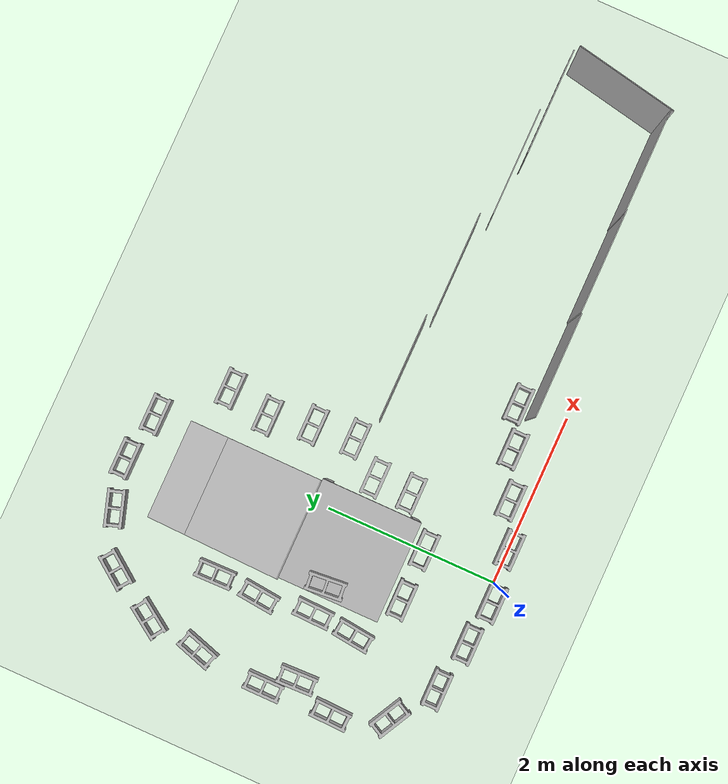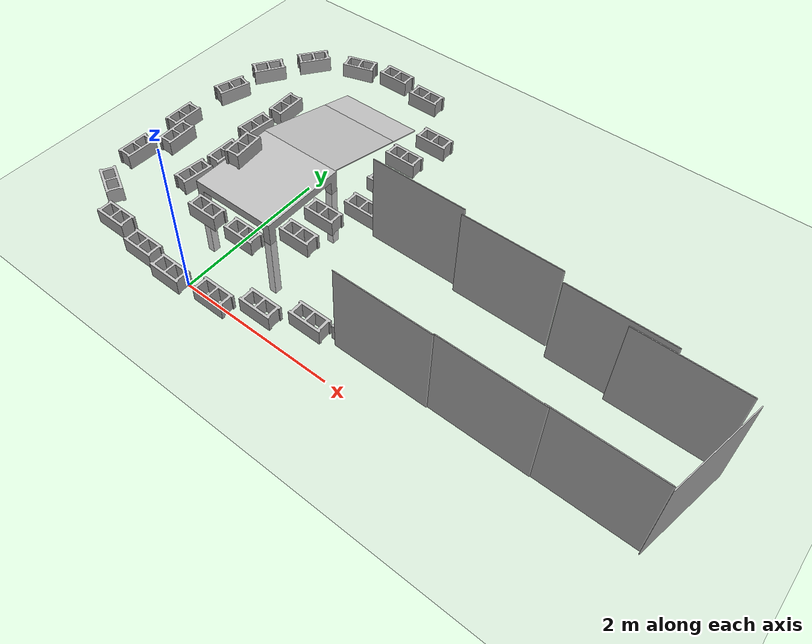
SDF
<sdf version="1.6">
 <world name="default">
  <light name="sun" type="directional">
   <pose>0 0 10 0 -0 0</pose>
   <diffuse>0.8 0.8 0.8 1</diffuse>
   <specular>0.2 0.2 0.2 1</specular>
   <attenuation>
    <range>1000</range>
    <constant>0.9</constant>
    <linear>0.01</linear>
    <quadratic>0.001</quadratic>
   </attenuation>
   <direction>-0.5 0.1 -0.9</direction>
  </light>
  <model name="ground_plane">
   <static>1</static>
   <link name="link">
    <collision name="collision">
     <geometry><plane><normal>0 0 1</normal><size>100 100</size></plane></geometry>
     <surface><friction><ode><mu>100</mu><mu2>50</mu2></ode></friction></surface>
    </collision>
    <visual name="visual">
     <cast_shadows>0</cast_shadows>
     <geometry><plane><normal>0 0 1</normal><size>100 100</size></plane></geometry>
     <material>
      <script><uri>file://media/materials/scripts/gazebo.material</uri><name>Gazebo/Grey</name></script>
     </material>
    </visual>
   </link>
  </model>
  <gravity>0 0 -9.8</gravity>
  <magnetic_field>6e-06 2.3e-05 -4.2e-05</magnetic_field>
  <atmosphere type="adiabatic"/>
  <physics name="default_physics" default="0" type="ode">
   <max_step_size>0.001</max_step_size>
   <real_time_factor>1</real_time_factor>
   <real_time_update_rate>1000</real_time_update_rate>
  </physics>
  <scene><ambient>0.4 0.4 0.4 1</ambient><background>0.7 0.7 0.7 1</background><shadows>1</shadows></scene>
  <spherical_coordinates>
   <surface_model>EARTH_WGS84</surface_model>
   <latitude_deg>0</latitude_deg>
   <longitude_deg>0</longitude_deg>
   <elevation>0</elevation>
   <heading_deg>0</heading_deg>
  </spherical_coordinates>
  <model name="cinder_block">
   <link name="link">
    <inertial>
     <pose>0 0 0.1016 0 -0 0</pose>
     <mass>5</mass>
     <inertia>
      <ixx>0.028705</ixx>
      <ixy>0</ixy>
      <iyy>0.073708</iyy>
      <ixz>0</ixz>
      <iyz>0</iyz>
      <izz>0.06908</izz>
     </inertia>
    </inertial>
    <visual name="visual">
     <geometry><mesh><uri>model://cinder_block/meshes/cinder_block.dae</uri></mesh></geometry>
    </visual>
    <collision name="left">
     <pose>0 -0.08465 0.1016 0 -0 0</pose>
     <geometry><box><size>0.43495 0.0339 0.2032</size></box></geometry>
     <surface>
      <contact><ode><max_vel>0.1</max_vel><min_depth>0.001</min_depth></ode></contact>
      <friction><ode><mu>1</mu><mu2>1</mu2></ode></friction>
     </surface>
    </collision>
    <collision name="right">
     <pose>0 0.08465 0.1016 0 -0 0</pose>
     <geometry><box><size>0.43495 0.0339 0.2032</size></box></geometry>
     <surface>
      <contact><ode><max_vel>0.1</max_vel><min_depth>0.001</min_depth></ode></contact>
      <friction><ode><mu>1</mu><mu2>1</mu2></ode></friction>
     </surface>
    </collision>
    <collision name="front">
     <pose>0.18625 0 0.1016 0 -0 0</pose>
     <geometry><box><size>0.0339 0.1354 0.203</size></box></geometry>
     <surface>
      <contact><ode><max_vel>0.1</max_vel><min_depth>0.001</min_depth></ode></contact>
      <friction><ode><mu>1</mu><mu2>1</mu2></ode></friction>
     </surface>
    </collision>
    <collision name="middle">
     <pose>0 0 0.1016 0 -0 0</pose>
     <geometry><box><size>0.0339 0.1354 0.203</size></box></geometry>
     <surface>
      <contact><ode><max_vel>0.1</max_vel><min_depth>0.001</min_depth></ode></contact>
      <friction><ode><mu>1</mu><mu2>1</mu2></ode></friction>
     </surface>
    </collision>
    <collision name="back">
     <pose>-0.18625 0 0.1016 0 -0 0</pose>
     <geometry><box><size>0.0339 0.1354 0.203</size></box></geometry>
     <surface>
      <contact><ode><max_vel>0.1</max_vel><min_depth>0.001</min_depth></ode></contact>
      <friction><ode><mu>1</mu><mu2>1</mu2></ode></friction>
     </surface>
    </collision>
   </link>
   <pose>-0.720374 -2.1e-05 -6e-06 -1e-06 2.9e-05 0</pose>
  </model>
  <model name="cinder_block_0">
   <link name="link">
    <inertial>
     <pose>0 0 0.1016 0 -0 0</pose>
     <mass>5</mass>
     <inertia>
      <ixx>0.028705</ixx>
      <ixy>0</ixy>
      <iyy>0.073708</iyy>
      <ixz>0</ixz>
      <iyz>0</iyz>
      <izz>0.06908</izz>
     </inertia>
    </inertial>
    <visual name="visual">
     <geometry><mesh><uri>model://cinder_block/meshes/cinder_block.dae</uri></mesh></geometry>
    </visual>
    <collision name="left">
     <pose>0 -0.08465 0.1016 0 -0 0</pose>
     <geometry><box><size>0.43495 0.0339 0.2032</size></box></geometry>
     <surface>
      <contact><ode><max_vel>0.1</max_vel><min_depth>0.001</min_depth></ode></contact>
      <friction><ode><mu>1</mu><mu2>1</mu2></ode></friction>
     </surface>
    </collision>
    <collision name="right">
     <pose>0 0.08465 0.1016 0 -0 0</pose>
     <geometry><box><size>0.43495 0.0339 0.2032</size></box></geometry>
     <surface>
      <contact><ode><max_vel>0.1</max_vel><min_depth>0.001</min_depth></ode></contact>
      <friction><ode><mu>1</mu><mu2>1</mu2></ode></friction>
     </surface>
    </collision>
    <collision name="front">
     <pose>0.18625 0 0.1016 0 -0 0</pose>
     <geometry><box><size>0.0339 0.1354 0.203</size></box></geometry>
     <surface>
      <contact><ode><max_vel>0.1</max_vel><min_depth>0.001</min_depth></ode></contact>
      <friction><ode><mu>1</mu><mu2>1</mu2></ode></friction>
     </surface>
    </collision>
    <collision name="middle">
     <pose>0 0 0.1016 0 -0 0</pose>
     <geometry><box><size>0.0339 0.1354 0.203</size></box></geometry>
     <surface>
      <contact><ode><max_vel>0.1</max_vel><min_depth>0.001</min_depth></ode></contact>
      <friction><ode><mu>1</mu><mu2>1</mu2></ode></friction>
     </surface>
    </collision>
    <collision name="back">
     <pose>-0.18625 0 0.1016 0 -0 0</pose>
     <geometry><box><size>0.0339 0.1354 0.203</size></box></geometry>
     <surface>
      <contact><ode><max_vel>0.1</max_vel><min_depth>0.001</min_depth></ode></contact>
      <friction><ode><mu>1</mu><mu2>1</mu2></ode></friction>
     </surface>
    </collision>
   </link>
   <pose>-1.31103 0.104421 -6e-06 -1e-06 2.9e-05 0</pose>
  </model>
  <model name="cinder_block_1">
   <link name="link">
    <inertial>
     <pose>0 0 0.1016 0 -0 0</pose>
     <mass>5</mass>
     <inertia>
      <ixx>0.028705</ixx>
      <ixy>0</ixy>
      <iyy>0.073708</iyy>
      <ixz>0</ixz>
      <iyz>0</iyz>
      <izz>0.06908</izz>
     </inertia>
    </inertial>
    <visual name="visual">
     <geometry><mesh><uri>model://cinder_block/meshes/cinder_block.dae</uri></mesh></geometry>
    </visual>
    <collision name="left">
     <pose>0 -0.08465 0.1016 0 -0 0</pose>
     <geometry><box><size>0.43495 0.0339 0.2032</size></box></geometry>
     <surface>
      <contact><ode><max_vel>0.1</max_vel><min_depth>0.001</min_depth></ode></contact>
      <friction><ode><mu>1</mu><mu2>1</mu2></ode></friction>
     </surface>
    </collision>
    <collision name="right">
     <pose>0 0.08465 0.1016 0 -0 0</pose>
     <geometry><box><size>0.43495 0.0339 0.2032</size></box></geometry>
     <surface>
      <contact><ode><max_vel>0.1</max_vel><min_depth>0.001</min_depth></ode></contact>
      <friction><ode><mu>1</mu><mu2>1</mu2></ode></friction>
     </surface>
    </collision>
    <collision name="front">
     <pose>0.18625 0 0.1016 0 -0 0</pose>
     <geometry><box><size>0.0339 0.1354 0.203</size></box></geometry>
     <surface>
      <contact><ode><max_vel>0.1</max_vel><min_depth>0.001</min_depth></ode></contact>
      <friction><ode><mu>1</mu><mu2>1</mu2></ode></friction>
     </surface>
    </collision>
    <collision name="middle">
     <pose>0 0 0.1016 0 -0 0</pose>
     <geometry><box><size>0.0339 0.1354 0.203</size></box></geometry>
     <surface>
      <contact><ode><max_vel>0.1</max_vel><min_depth>0.001</min_depth></ode></contact>
      <friction><ode><mu>1</mu><mu2>1</mu2></ode></friction>
     </surface>
    </collision>
    <collision name="back">
     <pose>-0.18625 0 0.1016 0 -0 0</pose>
     <geometry><box><size>0.0339 0.1354 0.203</size></box></geometry>
     <surface>
      <contact><ode><max_vel>0.1</max_vel><min_depth>0.001</min_depth></ode></contact>
      <friction><ode><mu>1</mu><mu2>1</mu2></ode></friction>
     </surface>
    </collision>
   </link>
   <pose>-1.8114 0.44481 -6e-06 -1e-05 2.5e-05 -0.487627</pose>
  </model>
  <model name="cinder_block_2">
   <link name="link">
    <inertial>
     <pose>0 0 0.1016 0 -0 0</pose>
     <mass>5</mass>
     <inertia>
      <ixx>0.028705</ixx>
      <ixy>0</ixy>
      <iyy>0.073708</iyy>
      <ixz>0</ixz>
      <iyz>0</iyz>
      <izz>0.06908</izz>
     </inertia>
    </inertial>
    <visual name="visual">
     <geometry><mesh><uri>model://cinder_block/meshes/cinder_block.dae</uri></mesh></geometry>
    </visual>
    <collision name="left">
     <pose>0 -0.08465 0.1016 0 -0 0</pose>
     <geometry><box><size>0.43495 0.0339 0.2032</size></box></geometry>
     <surface>
      <contact><ode><max_vel>0.1</max_vel><min_depth>0.001</min_depth></ode></contact>
      <friction><ode><mu>1</mu><mu2>1</mu2></ode></friction>
     </surface>
    </collision>
    <collision name="right">
     <pose>0 0.08465 0.1016 0 -0 0</pose>
     <geometry><box><size>0.43495 0.0339 0.2032</size></box></geometry>
     <surface>
      <contact><ode><max_vel>0.1</max_vel><min_depth>0.001</min_depth></ode></contact>
      <friction><ode><mu>1</mu><mu2>1</mu2></ode></friction>
     </surface>
    </collision>
    <collision name="front">
     <pose>0.18625 0 0.1016 0 -0 0</pose>
     <geometry><box><size>0.0339 0.1354 0.203</size></box></geometry>
     <surface>
      <contact><ode><max_vel>0.1</max_vel><min_depth>0.001</min_depth></ode></contact>
      <friction><ode><mu>1</mu><mu2>1</mu2></ode></friction>
     </surface>
    </collision>
    <collision name="middle">
     <pose>0 0 0.1016 0 -0 0</pose>
     <geometry><box><size>0.0339 0.1354 0.203</size></box></geometry>
     <surface>
      <contact><ode><max_vel>0.1</max_vel><min_depth>0.001</min_depth></ode></contact>
      <friction><ode><mu>1</mu><mu2>1</mu2></ode></friction>
     </surface>
    </collision>
    <collision name="back">
     <pose>-0.18625 0 0.1016 0 -0 0</pose>
     <geometry><box><size>0.0339 0.1354 0.203</size></box></geometry>
     <surface>
      <contact><ode><max_vel>0.1</max_vel><min_depth>0.001</min_depth></ode></contact>
      <friction><ode><mu>1</mu><mu2>1</mu2></ode></friction>
     </surface>
    </collision>
   </link>
   <pose>-0.201857 -0.063064 -6e-06 -1e-06 2.9e-05 0</pose>
  </model>
  <model name="cinder_block_3">
   <link name="link">
    <inertial>
     <pose>0 0 0.1016 0 -0 0</pose>
     <mass>5</mass>
     <inertia>
      <ixx>0.028705</ixx>
      <ixy>0</ixy>
      <iyy>0.073708</iyy>
      <ixz>0</ixz>
      <iyz>0</iyz>
      <izz>0.06908</izz>
     </inertia>
    </inertial>
    <visual name="visual">
     <geometry><mesh><uri>model://cinder_block/meshes/cinder_block.dae</uri></mesh></geometry>
    </visual>
    <collision name="left">
     <pose>0 -0.08465 0.1016 0 -0 0</pose>
     <geometry><box><size>0.43495 0.0339 0.2032</size></box></geometry>
     <surface>
      <contact><ode><max_vel>0.1</max_vel><min_depth>0.001</min_depth></ode></contact>
      <friction><ode><mu>1</mu><mu2>1</mu2></ode></friction>
     </surface>
    </collision>
    <collision name="right">
     <pose>0 0.08465 0.1016 0 -0 0</pose>
     <geometry><box><size>0.43495 0.0339 0.2032</size></box></geometry>
     <surface>
      <contact><ode><max_vel>0.1</max_vel><min_depth>0.001</min_depth></ode></contact>
      <friction><ode><mu>1</mu><mu2>1</mu2></ode></friction>
     </surface>
    </collision>
    <collision name="front">
     <pose>0.18625 0 0.1016 0 -0 0</pose>
     <geometry><box><size>0.0339 0.1354 0.203</size></box></geometry>
     <surface>
      <contact><ode><max_vel>0.1</max_vel><min_depth>0.001</min_depth></ode></contact>
      <friction><ode><mu>1</mu><mu2>1</mu2></ode></friction>
     </surface>
    </collision>
    <collision name="middle">
     <pose>0 0 0.1016 0 -0 0</pose>
     <geometry><box><size>0.0339 0.1354 0.203</size></box></geometry>
     <surface>
      <contact><ode><max_vel>0.1</max_vel><min_depth>0.001</min_depth></ode></contact>
      <friction><ode><mu>1</mu><mu2>1</mu2></ode></friction>
     </surface>
    </collision>
    <collision name="back">
     <pose>-0.18625 0 0.1016 0 -0 0</pose>
     <geometry><box><size>0.0339 0.1354 0.203</size></box></geometry>
     <surface>
      <contact><ode><max_vel>0.1</max_vel><min_depth>0.001</min_depth></ode></contact>
      <friction><ode><mu>1</mu><mu2>1</mu2></ode></friction>
     </surface>
    </collision>
   </link>
   <pose>0.409448 0.003088 -6e-06 -1e-06 2.9e-05 0</pose>
  </model>
  <model name="cinder_block_4">
   <link name="link">
    <inertial>
     <pose>0 0 0.1016 0 -0 0</pose>
     <mass>5</mass>
     <inertia>
      <ixx>0.028705</ixx>
      <ixy>0</ixy>
      <iyy>0.073708</iyy>
      <ixz>0</ixz>
      <iyz>0</iyz>
      <izz>0.06908</izz>
     </inertia>
    </inertial>
    <visual name="visual">
     <geometry><mesh><uri>model://cinder_block/meshes/cinder_block.dae</uri></mesh></geometry>
    </visual>
    <collision name="left">
     <pose>0 -0.08465 0.1016 0 -0 0</pose>
     <geometry><box><size>0.43495 0.0339 0.2032</size></box></geometry>
     <surface>
      <contact><ode><max_vel>0.1</max_vel><min_depth>0.001</min_depth></ode></contact>
      <friction><ode><mu>1</mu><mu2>1</mu2></ode></friction>
     </surface>
    </collision>
    <collision name="right">
     <pose>0 0.08465 0.1016 0 -0 0</pose>
     <geometry><box><size>0.43495 0.0339 0.2032</size></box></geometry>
     <surface>
      <contact><ode><max_vel>0.1</max_vel><min_depth>0.001</min_depth></ode></contact>
      <friction><ode><mu>1</mu><mu2>1</mu2></ode></friction>
     </surface>
    </collision>
    <collision name="front">
     <pose>0.18625 0 0.1016 0 -0 0</pose>
     <geometry><box><size>0.0339 0.1354 0.203</size></box></geometry>
     <surface>
      <contact><ode><max_vel>0.1</max_vel><min_depth>0.001</min_depth></ode></contact>
      <friction><ode><mu>1</mu><mu2>1</mu2></ode></friction>
     </surface>
    </collision>
    <collision name="middle">
     <pose>0 0 0.1016 0 -0 0</pose>
     <geometry><box><size>0.0339 0.1354 0.203</size></box></geometry>
     <surface>
      <contact><ode><max_vel>0.1</max_vel><min_depth>0.001</min_depth></ode></contact>
      <friction><ode><mu>1</mu><mu2>1</mu2></ode></friction>
     </surface>
    </collision>
    <collision name="back">
     <pose>-0.18625 0 0.1016 0 -0 0</pose>
     <geometry><box><size>0.0339 0.1354 0.203</size></box></geometry>
     <surface>
      <contact><ode><max_vel>0.1</max_vel><min_depth>0.001</min_depth></ode></contact>
      <friction><ode><mu>1</mu><mu2>1</mu2></ode></friction>
     </surface>
    </collision>
   </link>
   <pose>0.907571 0.210368 -6e-06 -1e-06 2.9e-05 0</pose>
  </model>
  <model name="cinder_block_5">
   <link name="link">
    <inertial>
     <pose>0 0 0.1016 0 -0 0</pose>
     <mass>5</mass>
     <inertia>
      <ixx>0.028705</ixx>
      <ixy>0</ixy>
      <iyy>0.073708</iyy>
      <ixz>0</ixz>
      <iyz>0</iyz>
      <izz>0.06908</izz>
     </inertia>
    </inertial>
    <visual name="visual">
     <geometry><mesh><uri>model://cinder_block/meshes/cinder_block.dae</uri></mesh></geometry>
    </visual>
    <collision name="left">
     <pose>0 -0.08465 0.1016 0 -0 0</pose>
     <geometry><box><size>0.43495 0.0339 0.2032</size></box></geometry>
     <surface>
      <contact><ode><max_vel>0.1</max_vel><min_depth>0.001</min_depth></ode></contact>
      <friction><ode><mu>1</mu><mu2>1</mu2></ode></friction>
     </surface>
    </collision>
    <collision name="right">
     <pose>0 0.08465 0.1016 0 -0 0</pose>
     <geometry><box><size>0.43495 0.0339 0.2032</size></box></geometry>
     <surface>
      <contact><ode><max_vel>0.1</max_vel><min_depth>0.001</min_depth></ode></contact>
      <friction><ode><mu>1</mu><mu2>1</mu2></ode></friction>
     </surface>
    </collision>
    <collision name="front">
     <pose>0.18625 0 0.1016 0 -0 0</pose>
     <geometry><box><size>0.0339 0.1354 0.203</size></box></geometry>
     <surface>
      <contact><ode><max_vel>0.1</max_vel><min_depth>0.001</min_depth></ode></contact>
      <friction><ode><mu>1</mu><mu2>1</mu2></ode></friction>
     </surface>
    </collision>
    <collision name="middle">
     <pose>0 0 0.1016 0 -0 0</pose>
     <geometry><box><size>0.0339 0.1354 0.203</size></box></geometry>
     <surface>
      <contact><ode><max_vel>0.1</max_vel><min_depth>0.001</min_depth></ode></contact>
      <friction><ode><mu>1</mu><mu2>1</mu2></ode></friction>
     </surface>
    </collision>
    <collision name="back">
     <pose>-0.18625 0 0.1016 0 -0 0</pose>
     <geometry><box><size>0.0339 0.1354 0.203</size></box></geometry>
     <surface>
      <contact><ode><max_vel>0.1</max_vel><min_depth>0.001</min_depth></ode></contact>
      <friction><ode><mu>1</mu><mu2>1</mu2></ode></friction>
     </surface>
    </collision>
   </link>
   <pose>1.43444 0.414241 -6e-06 -1e-06 2.9e-05 0</pose>
  </model>
  <model name="cinder_block_6">
   <link name="link">
    <inertial>
     <pose>0 0 0.1016 0 -0 0</pose>
     <mass>5</mass>
     <inertia>
      <ixx>0.028705</ixx>
      <ixy>0</ixy>
      <iyy>0.073708</iyy>
      <ixz>0</ixz>
      <iyz>0</iyz>
      <izz>0.06908</izz>
     </inertia>
    </inertial>
    <visual name="visual">
     <geometry><mesh><uri>model://cinder_block/meshes/cinder_block.dae</uri></mesh></geometry>
    </visual>
    <collision name="left">
     <pose>0 -0.08465 0.1016 0 -0 0</pose>
     <geometry><box><size>0.43495 0.0339 0.2032</size></box></geometry>
     <surface>
      <contact><ode><max_vel>0.1</max_vel><min_depth>0.001</min_depth></ode></contact>
      <friction><ode><mu>1</mu><mu2>1</mu2></ode></friction>
     </surface>
    </collision>
    <collision name="right">
     <pose>0 0.08465 0.1016 0 -0 0</pose>
     <geometry><box><size>0.43495 0.0339 0.2032</size></box></geometry>
     <surface>
      <contact><ode><max_vel>0.1</max_vel><min_depth>0.001</min_depth></ode></contact>
      <friction><ode><mu>1</mu><mu2>1</mu2></ode></friction>
     </surface>
    </collision>
    <collision name="front">
     <pose>0.18625 0 0.1016 0 -0 0</pose>
     <geometry><box><size>0.0339 0.1354 0.203</size></box></geometry>
     <surface>
      <contact><ode><max_vel>0.1</max_vel><min_depth>0.001</min_depth></ode></contact>
      <friction><ode><mu>1</mu><mu2>1</mu2></ode></friction>
     </surface>
    </collision>
    <collision name="middle">
     <pose>0 0 0.1016 0 -0 0</pose>
     <geometry><box><size>0.0339 0.1354 0.203</size></box></geometry>
     <surface>
      <contact><ode><max_vel>0.1</max_vel><min_depth>0.001</min_depth></ode></contact>
      <friction><ode><mu>1</mu><mu2>1</mu2></ode></friction>
     </surface>
    </collision>
    <collision name="back">
     <pose>-0.18625 0 0.1016 0 -0 0</pose>
     <geometry><box><size>0.0339 0.1354 0.203</size></box></geometry>
     <surface>
      <contact><ode><max_vel>0.1</max_vel><min_depth>0.001</min_depth></ode></contact>
      <friction><ode><mu>1</mu><mu2>1</mu2></ode></friction>
     </surface>
    </collision>
   </link>
   <pose>1.91072 0.564004 -6e-06 -1e-06 2.9e-05 0</pose>
  </model>
  <model name="cinder_block_7">
   <link name="link">
    <inertial>
     <pose>0 0 0.1016 0 -0 0</pose>
     <mass>5</mass>
     <inertia>
      <ixx>0.028705</ixx>
      <ixy>0</ixy>
      <iyy>0.073708</iyy>
      <ixz>0</ixz>
      <iyz>0</iyz>
      <izz>0.06908</izz>
     </inertia>
    </inertial>
    <visual name="visual">
     <geometry><mesh><uri>model://cinder_block/meshes/cinder_block.dae</uri></mesh></geometry>
    </visual>
    <collision name="left">
     <pose>0 -0.08465 0.1016 0 -0 0</pose>
     <geometry><box><size>0.43495 0.0339 0.2032</size></box></geometry>
     <surface>
      <contact><ode><max_vel>0.1</max_vel><min_depth>0.001</min_depth></ode></contact>
      <friction><ode><mu>1</mu><mu2>1</mu2></ode></friction>
     </surface>
    </collision>
    <collision name="right">
     <pose>0 0.08465 0.1016 0 -0 0</pose>
     <geometry><box><size>0.43495 0.0339 0.2032</size></box></geometry>
     <surface>
      <contact><ode><max_vel>0.1</max_vel><min_depth>0.001</min_depth></ode></contact>
      <friction><ode><mu>1</mu><mu2>1</mu2></ode></friction>
     </surface>
    </collision>
    <collision name="front">
     <pose>0.18625 0 0.1016 0 -0 0</pose>
     <geometry><box><size>0.0339 0.1354 0.203</size></box></geometry>
     <surface>
      <contact><ode><max_vel>0.1</max_vel><min_depth>0.001</min_depth></ode></contact>
      <friction><ode><mu>1</mu><mu2>1</mu2></ode></friction>
     </surface>
    </collision>
    <collision name="middle">
     <pose>0 0 0.1016 0 -0 0</pose>
     <geometry><box><size>0.0339 0.1354 0.203</size></box></geometry>
     <surface>
      <contact><ode><max_vel>0.1</max_vel><min_depth>0.001</min_depth></ode></contact>
      <friction><ode><mu>1</mu><mu2>1</mu2></ode></friction>
     </surface>
    </collision>
    <collision name="back">
     <pose>-0.18625 0 0.1016 0 -0 0</pose>
     <geometry><box><size>0.0339 0.1354 0.203</size></box></geometry>
     <surface>
      <contact><ode><max_vel>0.1</max_vel><min_depth>0.001</min_depth></ode></contact>
      <friction><ode><mu>1</mu><mu2>1</mu2></ode></friction>
     </surface>
    </collision>
   </link>
   <pose>-2.04034 1.05442 -6e-06 -3e-05 -1e-06 -1.59941</pose>
  </model>
  <model name="cinder_block_8">
   <link name="link">
    <inertial>
     <pose>0 0 0.1016 0 -0 0</pose>
     <mass>5</mass>
     <inertia>
      <ixx>0.028705</ixx>
      <ixy>0</ixy>
      <iyy>0.073708</iyy>
      <ixz>0</ixz>
      <iyz>0</iyz>
      <izz>0.06908</izz>
     </inertia>
    </inertial>
    <visual name="visual">
     <geometry><mesh><uri>model://cinder_block/meshes/cinder_block.dae</uri></mesh></geometry>
    </visual>
    <collision name="left">
     <pose>0 -0.08465 0.1016 0 -0 0</pose>
     <geometry><box><size>0.43495 0.0339 0.2032</size></box></geometry>
     <surface>
      <contact><ode><max_vel>0.1</max_vel><min_depth>0.001</min_depth></ode></contact>
      <friction><ode><mu>1</mu><mu2>1</mu2></ode></friction>
     </surface>
    </collision>
    <collision name="right">
     <pose>0 0.08465 0.1016 0 -0 0</pose>
     <geometry><box><size>0.43495 0.0339 0.2032</size></box></geometry>
     <surface>
      <contact><ode><max_vel>0.1</max_vel><min_depth>0.001</min_depth></ode></contact>
      <friction><ode><mu>1</mu><mu2>1</mu2></ode></friction>
     </surface>
    </collision>
    <collision name="front">
     <pose>0.18625 0 0.1016 0 -0 0</pose>
     <geometry><box><size>0.0339 0.1354 0.203</size></box></geometry>
     <surface>
      <contact><ode><max_vel>0.1</max_vel><min_depth>0.001</min_depth></ode></contact>
      <friction><ode><mu>1</mu><mu2>1</mu2></ode></friction>
     </surface>
    </collision>
    <collision name="middle">
     <pose>0 0 0.1016 0 -0 0</pose>
     <geometry><box><size>0.0339 0.1354 0.203</size></box></geometry>
     <surface>
      <contact><ode><max_vel>0.1</max_vel><min_depth>0.001</min_depth></ode></contact>
      <friction><ode><mu>1</mu><mu2>1</mu2></ode></friction>
     </surface>
    </collision>
    <collision name="back">
     <pose>-0.18625 0 0.1016 0 -0 0</pose>
     <geometry><box><size>0.0339 0.1354 0.203</size></box></geometry>
     <surface>
      <contact><ode><max_vel>0.1</max_vel><min_depth>0.001</min_depth></ode></contact>
      <friction><ode><mu>1</mu><mu2>1</mu2></ode></friction>
     </surface>
    </collision>
   </link>
   <pose>-2.06265 1.85109 -6e-06 -3e-05 -1e-06 -1.57236</pose>
  </model>
  <model name="nist_maze_wall_120">
   <static>1</static>
   <link name="nist_maze_wall_120_link">
    <collision name="collision">
     <geometry>
      <mesh><uri>model://nist_maze_wall_120/meshes/nist_maze_wall_120.dae</uri><scale>1 1 1</scale></mesh>
     </geometry>
    </collision>
    <visual name="visual">
     <geometry>
      <mesh><uri>model://nist_maze_wall_120/meshes/nist_maze_wall_120.dae</uri><scale>1 1 1</scale></mesh>
     </geometry>
    </visual>
   </link>
   <pose>2.37571 -0.184064 0 0 -0 0</pose>
  </model>
  <model name="nist_maze_wall_120_0">
   <static>1</static>
   <link name="nist_maze_wall_120_link">
    <collision name="collision">
     <geometry>
      <mesh><uri>model://nist_maze_wall_120/meshes/nist_maze_wall_120.dae</uri><scale>1 1 1</scale></mesh>
     </geometry>
    </collision>
    <visual name="visual">
     <geometry>
      <mesh><uri>model://nist_maze_wall_120/meshes/nist_maze_wall_120.dae</uri><scale>1 1 1</scale></mesh>
     </geometry>
    </visual>
   </link>
   <pose>3.56261 -0.171949 0 0 -0 0</pose>
  </model>
  <model name="nist_maze_wall_120_1">
   <static>1</static>
   <link name="nist_maze_wall_120_link">
    <collision name="collision">
     <geometry>
      <mesh><uri>model://nist_maze_wall_120/meshes/nist_maze_wall_120.dae</uri><scale>1 1 1</scale></mesh>
     </geometry>
    </collision>
    <visual name="visual">
     <geometry>
      <mesh><uri>model://nist_maze_wall_120/meshes/nist_maze_wall_120.dae</uri><scale>1 1 1</scale></mesh>
     </geometry>
    </visual>
   </link>
   <pose>4.69666 -0.164227 0 0 -0 0</pose>
  </model>
  <model name="nist_maze_wall_120_2">
   <static>1</static>
   <link name="nist_maze_wall_120_link">
    <collision name="collision">
     <geometry>
      <mesh><uri>model://nist_maze_wall_120/meshes/nist_maze_wall_120.dae</uri><scale>1 1 1</scale></mesh>
     </geometry>
    </collision>
    <visual name="visual">
     <geometry>
      <mesh><uri>model://nist_maze_wall_120/meshes/nist_maze_wall_120.dae</uri><scale>1 1 1</scale></mesh>
     </geometry>
    </visual>
   </link>
   <pose>6.00334 0.871408 0 0 -0 1.37919</pose>
  </model>
  <model name="nist_maze_wall_120_3">
   <static>1</static>
   <link name="nist_maze_wall_120_link">
    <collision name="collision">
     <geometry>
      <mesh><uri>model://nist_maze_wall_120/meshes/nist_maze_wall_120.dae</uri><scale>1 1 1</scale></mesh>
     </geometry>
    </collision>
    <visual name="visual">
     <geometry>
      <mesh><uri>model://nist_maze_wall_120/meshes/nist_maze_wall_120.dae</uri><scale>1 1 1</scale></mesh>
     </geometry>
    </visual>
   </link>
   <pose>4.86569 1.01272 0 0 -0 0</pose>
  </model>
  <model name="nist_maze_wall_120_4">
   <static>1</static>
   <link name="nist_maze_wall_120_link">
    <collision name="collision">
     <geometry>
      <mesh><uri>model://nist_maze_wall_120/meshes/nist_maze_wall_120.dae</uri><scale>1 1 1</scale></mesh>
     </geometry>
    </collision>
    <visual name="visual">
     <geometry>
      <mesh><uri>model://nist_maze_wall_120/meshes/nist_maze_wall_120.dae</uri><scale>1 1 1</scale></mesh>
     </geometry>
    </visual>
   </link>
   <pose>4.14425 1.08064 0 0 -0 0</pose>
  </model>
  <model name="nist_maze_wall_120_5">
   <static>1</static>
   <link name="nist_maze_wall_120_link">
    <collision name="collision">
     <geometry>
      <mesh><uri>model://nist_maze_wall_120/meshes/nist_maze_wall_120.dae</uri><scale>1 1 1</scale></mesh>
     </geometry>
    </collision>
    <visual name="visual">
     <geometry>
      <mesh><uri>model://nist_maze_wall_120/meshes/nist_maze_wall_120.dae</uri><scale>1 1 1</scale></mesh>
     </geometry>
    </visual>
   </link>
   <pose>2.8932 1.20612 0 0 -0 0</pose>
  </model>
  <model name="nist_maze_wall_120_6">
   <static>1</static>
   <link name="nist_maze_wall_120_link">
    <collision name="collision">
     <geometry>
      <mesh><uri>model://nist_maze_wall_120/meshes/nist_maze_wall_120.dae</uri><scale>1 1 1</scale></mesh>
     </geometry>
    </collision>
    <visual name="visual">
     <geometry>
      <mesh><uri>model://nist_maze_wall_120/meshes/nist_maze_wall_120.dae</uri><scale>1 1 1</scale></mesh>
     </geometry>
    </visual>
   </link>
   <pose>1.69448 1.28024 0 0 -0 0</pose>
  </model>
  <model name="nist_elevated_floor_120">
   <static>1</static>
   <link name="nist_elevated_floor_120">
    <collision name="collision">
     <geometry>
      <mesh><uri>model://nist_elevated_floor_120/meshes/nist_elevated_floor_120.dae</uri><scale>1 1 1</scale></mesh>
     </geometry>
    </collision>
    <visual name="visual">
     <geometry>
      <mesh><uri>model://nist_elevated_floor_120/meshes/nist_elevated_floor_120.dae</uri><scale>1 1 1</scale></mesh>
     </geometry>
    </visual>
   </link>
   <pose>-0.307594 1.59992 -0.889932 0 -0 0</pose>
  </model>
  <model name="cinder_block_9">
   <link name="link">
    <inertial>
     <pose>0 0 0.1016 0 -0 0</pose>
     <mass>5</mass>
     <inertia>
      <ixx>0.028705</ixx>
      <ixy>0</ixy>
      <iyy>0.073708</iyy>
      <ixz>0</ixz>
      <iyz>0</iyz>
      <izz>0.06908</izz>
     </inertia>
    </inertial>
    <visual name="visual">
     <geometry><mesh><uri>model://cinder_block/meshes/cinder_block.dae</uri></mesh></geometry>
    </visual>
    <collision name="left">
     <pose>0 -0.08465 0.1016 0 -0 0</pose>
     <geometry><box><size>0.43495 0.0339 0.2032</size></box></geometry>
     <surface>
      <contact><ode><max_vel>0.1</max_vel><min_depth>0.001</min_depth></ode></contact>
      <friction><ode><mu>1</mu><mu2>1</mu2></ode></friction>
     </surface>
    </collision>
    <collision name="right">
     <pose>0 0.08465 0.1016 0 -0 0</pose>
     <geometry><box><size>0.43495 0.0339 0.2032</size></box></geometry>
     <surface>
      <contact><ode><max_vel>0.1</max_vel><min_depth>0.001</min_depth></ode></contact>
      <friction><ode><mu>1</mu><mu2>1</mu2></ode></friction>
     </surface>
    </collision>
    <collision name="front">
     <pose>0.18625 0 0.1016 0 -0 0</pose>
     <geometry><box><size>0.0339 0.1354 0.203</size></box></geometry>
     <surface>
      <contact><ode><max_vel>0.1</max_vel><min_depth>0.001</min_depth></ode></contact>
      <friction><ode><mu>1</mu><mu2>1</mu2></ode></friction>
     </surface>
    </collision>
    <collision name="middle">
     <pose>0 0 0.1016 0 -0 0</pose>
     <geometry><box><size>0.0339 0.1354 0.203</size></box></geometry>
     <surface>
      <contact><ode><max_vel>0.1</max_vel><min_depth>0.001</min_depth></ode></contact>
      <friction><ode><mu>1</mu><mu2>1</mu2></ode></friction>
     </surface>
    </collision>
    <collision name="back">
     <pose>-0.18625 0 0.1016 0 -0 0</pose>
     <geometry><box><size>0.0339 0.1354 0.203</size></box></geometry>
     <surface>
      <contact><ode><max_vel>0.1</max_vel><min_depth>0.001</min_depth></ode></contact>
      <friction><ode><mu>1</mu><mu2>1</mu2></ode></friction>
     </surface>
    </collision>
   </link>
   <pose>0.530702 1.23913 -6e-06 -1e-06 2.8e-05 -0</pose>
  </model>
  <model name="cinder_block_10">
   <link name="link">
    <inertial>
     <pose>0 0 0.1016 0 -0 0</pose>
     <mass>5</mass>
     <inertia>
      <ixx>0.028705</ixx>
      <ixy>0</ixy>
      <iyy>0.073708</iyy>
      <ixz>0</ixz>
      <iyz>0</iyz>
      <izz>0.06908</izz>
     </inertia>
    </inertial>
    <visual name="visual">
     <geometry><mesh><uri>model://cinder_block/meshes/cinder_block.dae</uri></mesh></geometry>
    </visual>
    <collision name="left">
     <pose>0 -0.08465 0.1016 0 -0 0</pose>
     <geometry><box><size>0.43495 0.0339 0.2032</size></box></geometry>
     <surface>
      <contact><ode><max_vel>0.1</max_vel><min_depth>0.001</min_depth></ode></contact>
      <friction><ode><mu>1</mu><mu2>1</mu2></ode></friction>
     </surface>
    </collision>
    <collision name="right">
     <pose>0 0.08465 0.1016 0 -0 0</pose>
     <geometry><box><size>0.43495 0.0339 0.2032</size></box></geometry>
     <surface>
      <contact><ode><max_vel>0.1</max_vel><min_depth>0.001</min_depth></ode></contact>
      <friction><ode><mu>1</mu><mu2>1</mu2></ode></friction>
     </surface>
    </collision>
    <collision name="front">
     <pose>0.18625 0 0.1016 0 -0 0</pose>
     <geometry><box><size>0.0339 0.1354 0.203</size></box></geometry>
     <surface>
      <contact><ode><max_vel>0.1</max_vel><min_depth>0.001</min_depth></ode></contact>
      <friction><ode><mu>1</mu><mu2>1</mu2></ode></friction>
     </surface>
    </collision>
    <collision name="middle">
     <pose>0 0 0.1016 0 -0 0</pose>
     <geometry><box><size>0.0339 0.1354 0.203</size></box></geometry>
     <surface>
      <contact><ode><max_vel>0.1</max_vel><min_depth>0.001</min_depth></ode></contact>
      <friction><ode><mu>1</mu><mu2>1</mu2></ode></friction>
     </surface>
    </collision>
    <collision name="back">
     <pose>-0.18625 0 0.1016 0 -0 0</pose>
     <geometry><box><size>0.0339 0.1354 0.203</size></box></geometry>
     <surface>
      <contact><ode><max_vel>0.1</max_vel><min_depth>0.001</min_depth></ode></contact>
      <friction><ode><mu>1</mu><mu2>1</mu2></ode></friction>
     </surface>
    </collision>
   </link>
   <pose>0.525258 1.67182 -6e-06 -1e-06 2.8e-05 -0</pose>
  </model>
  <model name="cinder_block_11">
   <link name="link">
    <inertial>
     <pose>0 0 0.1016 0 -0 0</pose>
     <mass>5</mass>
     <inertia>
      <ixx>0.028705</ixx>
      <ixy>0</ixy>
      <iyy>0.073708</iyy>
      <ixz>0</ixz>
      <iyz>0</iyz>
      <izz>0.06908</izz>
     </inertia>
    </inertial>
    <visual name="visual">
     <geometry><mesh><uri>model://cinder_block/meshes/cinder_block.dae</uri></mesh></geometry>
    </visual>
    <collision name="left">
     <pose>0 -0.08465 0.1016 0 -0 0</pose>
     <geometry><box><size>0.43495 0.0339 0.2032</size></box></geometry>
     <surface>
      <contact><ode><max_vel>0.1</max_vel><min_depth>0.001</min_depth></ode></contact>
      <friction><ode><mu>1</mu><mu2>1</mu2></ode></friction>
     </surface>
    </collision>
    <collision name="right">
     <pose>0 0.08465 0.1016 0 -0 0</pose>
     <geometry><box><size>0.43495 0.0339 0.2032</size></box></geometry>
     <surface>
      <contact><ode><max_vel>0.1</max_vel><min_depth>0.001</min_depth></ode></contact>
      <friction><ode><mu>1</mu><mu2>1</mu2></ode></friction>
     </surface>
    </collision>
    <collision name="front">
     <pose>0.18625 0 0.1016 0 -0 0</pose>
     <geometry><box><size>0.0339 0.1354 0.203</size></box></geometry>
     <surface>
      <contact><ode><max_vel>0.1</max_vel><min_depth>0.001</min_depth></ode></contact>
      <friction><ode><mu>1</mu><mu2>1</mu2></ode></friction>
     </surface>
    </collision>
    <collision name="middle">
     <pose>0 0 0.1016 0 -0 0</pose>
     <geometry><box><size>0.0339 0.1354 0.203</size></box></geometry>
     <surface>
      <contact><ode><max_vel>0.1</max_vel><min_depth>0.001</min_depth></ode></contact>
      <friction><ode><mu>1</mu><mu2>1</mu2></ode></friction>
     </surface>
    </collision>
    <collision name="back">
     <pose>-0.18625 0 0.1016 0 -0 0</pose>
     <geometry><box><size>0.0339 0.1354 0.203</size></box></geometry>
     <surface>
      <contact><ode><max_vel>0.1</max_vel><min_depth>0.001</min_depth></ode></contact>
      <friction><ode><mu>1</mu><mu2>1</mu2></ode></friction>
     </surface>
    </collision>
   </link>
   <pose>0.020907 0.854106 -6e-06 -1e-06 2.8e-05 -0</pose>
  </model>
  <model name="cinder_block_12">
   <link name="link">
    <inertial>
     <pose>0 0 0.1016 0 -0 0</pose>
     <mass>5</mass>
     <inertia>
      <ixx>0.028705</ixx>
      <ixy>0</ixy>
      <iyy>0.073708</iyy>
      <ixz>0</ixz>
      <iyz>0</iyz>
      <izz>0.06908</izz>
     </inertia>
    </inertial>
    <visual name="visual">
     <geometry><mesh><uri>model://cinder_block/meshes/cinder_block.dae</uri></mesh></geometry>
    </visual>
    <collision name="left">
     <pose>0 -0.08465 0.1016 0 -0 0</pose>
     <geometry><box><size>0.43495 0.0339 0.2032</size></box></geometry>
     <surface>
      <contact><ode><max_vel>0.1</max_vel><min_depth>0.001</min_depth></ode></contact>
      <friction><ode><mu>1</mu><mu2>1</mu2></ode></friction>
     </surface>
    </collision>
    <collision name="right">
     <pose>0 0.08465 0.1016 0 -0 0</pose>
     <geometry><box><size>0.43495 0.0339 0.2032</size></box></geometry>
     <surface>
      <contact><ode><max_vel>0.1</max_vel><min_depth>0.001</min_depth></ode></contact>
      <friction><ode><mu>1</mu><mu2>1</mu2></ode></friction>
     </surface>
    </collision>
    <collision name="front">
     <pose>0.18625 0 0.1016 0 -0 0</pose>
     <geometry><box><size>0.0339 0.1354 0.203</size></box></geometry>
     <surface>
      <contact><ode><max_vel>0.1</max_vel><min_depth>0.001</min_depth></ode></contact>
      <friction><ode><mu>1</mu><mu2>1</mu2></ode></friction>
     </surface>
    </collision>
    <collision name="middle">
     <pose>0 0 0.1016 0 -0 0</pose>
     <geometry><box><size>0.0339 0.1354 0.203</size></box></geometry>
     <surface>
      <contact><ode><max_vel>0.1</max_vel><min_depth>0.001</min_depth></ode></contact>
      <friction><ode><mu>1</mu><mu2>1</mu2></ode></friction>
     </surface>
    </collision>
    <collision name="back">
     <pose>-0.18625 0 0.1016 0 -0 0</pose>
     <geometry><box><size>0.0339 0.1354 0.203</size></box></geometry>
     <surface>
      <contact><ode><max_vel>0.1</max_vel><min_depth>0.001</min_depth></ode></contact>
      <friction><ode><mu>1</mu><mu2>1</mu2></ode></friction>
     </surface>
    </collision>
   </link>
   <pose>-0.577262 0.856201 -6e-06 -1e-06 2.8e-05 -0</pose>
  </model>
  <model name="cinder_block_13">
   <link name="link">
    <inertial>
     <pose>0 0 0.1016 0 -0 0</pose>
     <mass>5</mass>
     <inertia>
      <ixx>0.028705</ixx>
      <ixy>0</ixy>
      <iyy>0.073708</iyy>
      <ixz>0</ixz>
      <iyz>0</iyz>
      <izz>0.06908</izz>
     </inertia>
    </inertial>
    <visual name="visual">
     <geometry><mesh><uri>model://cinder_block/meshes/cinder_block.dae</uri></mesh></geometry>
    </visual>
    <collision name="left">
     <pose>0 -0.08465 0.1016 0 -0 0</pose>
     <geometry><box><size>0.43495 0.0339 0.2032</size></box></geometry>
     <surface>
      <contact><ode><max_vel>0.1</max_vel><min_depth>0.001</min_depth></ode></contact>
      <friction><ode><mu>1</mu><mu2>1</mu2></ode></friction>
     </surface>
    </collision>
    <collision name="right">
     <pose>0 0.08465 0.1016 0 -0 0</pose>
     <geometry><box><size>0.43495 0.0339 0.2032</size></box></geometry>
     <surface>
      <contact><ode><max_vel>0.1</max_vel><min_depth>0.001</min_depth></ode></contact>
      <friction><ode><mu>1</mu><mu2>1</mu2></ode></friction>
     </surface>
    </collision>
    <collision name="front">
     <pose>0.18625 0 0.1016 0 -0 0</pose>
     <geometry><box><size>0.0339 0.1354 0.203</size></box></geometry>
     <surface>
      <contact><ode><max_vel>0.1</max_vel><min_depth>0.001</min_depth></ode></contact>
      <friction><ode><mu>1</mu><mu2>1</mu2></ode></friction>
     </surface>
    </collision>
    <collision name="middle">
     <pose>0 0 0.1016 0 -0 0</pose>
     <geometry><box><size>0.0339 0.1354 0.203</size></box></geometry>
     <surface>
      <contact><ode><max_vel>0.1</max_vel><min_depth>0.001</min_depth></ode></contact>
      <friction><ode><mu>1</mu><mu2>1</mu2></ode></friction>
     </surface>
    </collision>
    <collision name="back">
     <pose>-0.18625 0 0.1016 0 -0 0</pose>
     <geometry><box><size>0.0339 0.1354 0.203</size></box></geometry>
     <surface>
      <contact><ode><max_vel>0.1</max_vel><min_depth>0.001</min_depth></ode></contact>
      <friction><ode><mu>1</mu><mu2>1</mu2></ode></friction>
     </surface>
    </collision>
   </link>
   <pose>-1.84874 1.54636 -6e-06 -2.9e-05 1e-06 -1.53726</pose>
  </model>
  <model name="cinder_block_14">
   <link name="link">
    <inertial>
     <pose>0 0 0.1016 0 -0 0</pose>
     <mass>5</mass>
     <inertia>
      <ixx>0.028705</ixx>
      <ixy>0</ixy>
      <iyy>0.073708</iyy>
      <ixz>0</ixz>
      <iyz>0</iyz>
      <izz>0.06908</izz>
     </inertia>
    </inertial>
    <visual name="visual">
     <geometry><mesh><uri>model://cinder_block/meshes/cinder_block.dae</uri></mesh></geometry>
    </visual>
    <collision name="left">
     <pose>0 -0.08465 0.1016 0 -0 0</pose>
     <geometry><box><size>0.43495 0.0339 0.2032</size></box></geometry>
     <surface>
      <contact><ode><max_vel>0.1</max_vel><min_depth>0.001</min_depth></ode></contact>
      <friction><ode><mu>1</mu><mu2>1</mu2></ode></friction>
     </surface>
    </collision>
    <collision name="right">
     <pose>0 0.08465 0.1016 0 -0 0</pose>
     <geometry><box><size>0.43495 0.0339 0.2032</size></box></geometry>
     <surface>
      <contact><ode><max_vel>0.1</max_vel><min_depth>0.001</min_depth></ode></contact>
      <friction><ode><mu>1</mu><mu2>1</mu2></ode></friction>
     </surface>
    </collision>
    <collision name="front">
     <pose>0.18625 0 0.1016 0 -0 0</pose>
     <geometry><box><size>0.0339 0.1354 0.203</size></box></geometry>
     <surface>
      <contact><ode><max_vel>0.1</max_vel><min_depth>0.001</min_depth></ode></contact>
      <friction><ode><mu>1</mu><mu2>1</mu2></ode></friction>
     </surface>
    </collision>
    <collision name="middle">
     <pose>0 0 0.1016 0 -0 0</pose>
     <geometry><box><size>0.0339 0.1354 0.203</size></box></geometry>
     <surface>
      <contact><ode><max_vel>0.1</max_vel><min_depth>0.001</min_depth></ode></contact>
      <friction><ode><mu>1</mu><mu2>1</mu2></ode></friction>
     </surface>
    </collision>
    <collision name="back">
     <pose>-0.18625 0 0.1016 0 -0 0</pose>
     <geometry><box><size>0.0339 0.1354 0.203</size></box></geometry>
     <surface>
      <contact><ode><max_vel>0.1</max_vel><min_depth>0.001</min_depth></ode></contact>
      <friction><ode><mu>1</mu><mu2>1</mu2></ode></friction>
     </surface>
    </collision>
   </link>
   <pose>-0.760176 1.6809 0.309529 0 -0 1.65816</pose>
  </model>
  <model name="nist_simple_ramp_120">
   <static>1</static>
   <link name="nist_simple_ramp_120_link">
    <collision name="collision">
     <geometry>
      <mesh><uri>model://nist_simple_ramp_120/meshes/nist_simple_ramp_120.dae</uri><scale>1 1 1</scale></mesh>
     </geometry>
    </collision>
    <visual name="visual">
     <geometry>
      <mesh><uri>model://nist_simple_ramp_120/meshes/nist_simple_ramp_120.dae</uri><scale>1 1 1</scale></mesh>
     </geometry>
    </visual>
   </link>
   <pose>-0.331889 2.48219 -0.221987 -1.04959 0 0</pose>
  </model>
  <model name="cinder_block_15">
   <link name="link">
    <inertial>
     <pose>0 0 0.1016 0 -0 0</pose>
     <mass>5</mass>
     <inertia>
      <ixx>0.028705</ixx>
      <ixy>0</ixy>
      <iyy>0.073708</iyy>
      <ixz>0</ixz>
      <iyz>0</iyz>
      <izz>0.06908</izz>
     </inertia>
    </inertial>
    <visual name="visual">
     <geometry><mesh><uri>model://cinder_block/meshes/cinder_block.dae</uri></mesh></geometry>
    </visual>
    <collision name="left">
     <pose>0 -0.08465 0.1016 0 -0 0</pose>
     <geometry><box><size>0.43495 0.0339 0.2032</size></box></geometry>
     <surface>
      <contact><ode><max_vel>0.1</max_vel><min_depth>0.001</min_depth></ode></contact>
      <friction><ode><mu>1</mu><mu2>1</mu2></ode></friction>
     </surface>
    </collision>
    <collision name="right">
     <pose>0 0.08465 0.1016 0 -0 0</pose>
     <geometry><box><size>0.43495 0.0339 0.2032</size></box></geometry>
     <surface>
      <contact><ode><max_vel>0.1</max_vel><min_depth>0.001</min_depth></ode></contact>
      <friction><ode><mu>1</mu><mu2>1</mu2></ode></friction>
     </surface>
    </collision>
    <collision name="front">
     <pose>0.18625 0 0.1016 0 -0 0</pose>
     <geometry><box><size>0.0339 0.1354 0.203</size></box></geometry>
     <surface>
      <contact><ode><max_vel>0.1</max_vel><min_depth>0.001</min_depth></ode></contact>
      <friction><ode><mu>1</mu><mu2>1</mu2></ode></friction>
     </surface>
    </collision>
    <collision name="middle">
     <pose>0 0 0.1016 0 -0 0</pose>
     <geometry><box><size>0.0339 0.1354 0.203</size></box></geometry>
     <surface>
      <contact><ode><max_vel>0.1</max_vel><min_depth>0.001</min_depth></ode></contact>
      <friction><ode><mu>1</mu><mu2>1</mu2></ode></friction>
     </surface>
    </collision>
    <collision name="back">
     <pose>-0.18625 0 0.1016 0 -0 0</pose>
     <geometry><box><size>0.0339 0.1354 0.203</size></box></geometry>
     <surface>
      <contact><ode><max_vel>0.1</max_vel><min_depth>0.001</min_depth></ode></contact>
      <friction><ode><mu>1</mu><mu2>1</mu2></ode></friction>
     </surface>
    </collision>
   </link>
   <pose>0.824846 2.04753 0 0 -0 0</pose>
  </model>
  <model name="cinder_block_16">
   <link name="link">
    <inertial>
     <pose>0 0 0.1016 0 -0 0</pose>
     <mass>5</mass>
     <inertia>
      <ixx>0.028705</ixx>
      <ixy>0</ixy>
      <iyy>0.073708</iyy>
      <ixz>0</ixz>
      <iyz>0</iyz>
      <izz>0.06908</izz>
     </inertia>
    </inertial>
    <visual name="visual">
     <geometry><mesh><uri>model://cinder_block/meshes/cinder_block.dae</uri></mesh></geometry>
    </visual>
    <collision name="left">
     <pose>0 -0.08465 0.1016 0 -0 0</pose>
     <geometry><box><size>0.43495 0.0339 0.2032</size></box></geometry>
     <surface>
      <contact><ode><max_vel>0.1</max_vel><min_depth>0.001</min_depth></ode></contact>
      <friction><ode><mu>1</mu><mu2>1</mu2></ode></friction>
     </surface>
    </collision>
    <collision name="right">
     <pose>0 0.08465 0.1016 0 -0 0</pose>
     <geometry><box><size>0.43495 0.0339 0.2032</size></box></geometry>
     <surface>
      <contact><ode><max_vel>0.1</max_vel><min_depth>0.001</min_depth></ode></contact>
      <friction><ode><mu>1</mu><mu2>1</mu2></ode></friction>
     </surface>
    </collision>
    <collision name="front">
     <pose>0.18625 0 0.1016 0 -0 0</pose>
     <geometry><box><size>0.0339 0.1354 0.203</size></box></geometry>
     <surface>
      <contact><ode><max_vel>0.1</max_vel><min_depth>0.001</min_depth></ode></contact>
      <friction><ode><mu>1</mu><mu2>1</mu2></ode></friction>
     </surface>
    </collision>
    <collision name="middle">
     <pose>0 0 0.1016 0 -0 0</pose>
     <geometry><box><size>0.0339 0.1354 0.203</size></box></geometry>
     <surface>
      <contact><ode><max_vel>0.1</max_vel><min_depth>0.001</min_depth></ode></contact>
      <friction><ode><mu>1</mu><mu2>1</mu2></ode></friction>
     </surface>
    </collision>
    <collision name="back">
     <pose>-0.18625 0 0.1016 0 -0 0</pose>
     <geometry><box><size>0.0339 0.1354 0.203</size></box></geometry>
     <surface>
      <contact><ode><max_vel>0.1</max_vel><min_depth>0.001</min_depth></ode></contact>
      <friction><ode><mu>1</mu><mu2>1</mu2></ode></friction>
     </surface>
    </collision>
   </link>
   <pose>0.773398 2.53608 0 0 -0 0</pose>
  </model>
  <model name="cinder_block_17">
   <link name="link">
    <inertial>
     <pose>0 0 0.1016 0 -0 0</pose>
     <mass>5</mass>
     <inertia>
      <ixx>0.028705</ixx>
      <ixy>0</ixy>
      <iyy>0.073708</iyy>
      <ixz>0</ixz>
      <iyz>0</iyz>
      <izz>0.06908</izz>
     </inertia>
    </inertial>
    <visual name="visual">
     <geometry><mesh><uri>model://cinder_block/meshes/cinder_block.dae</uri></mesh></geometry>
    </visual>
    <collision name="left">
     <pose>0 -0.08465 0.1016 0 -0 0</pose>
     <geometry><box><size>0.43495 0.0339 0.2032</size></box></geometry>
     <surface>
      <contact><ode><max_vel>0.1</max_vel><min_depth>0.001</min_depth></ode></contact>
      <friction><ode><mu>1</mu><mu2>1</mu2></ode></friction>
     </surface>
    </collision>
    <collision name="right">
     <pose>0 0.08465 0.1016 0 -0 0</pose>
     <geometry><box><size>0.43495 0.0339 0.2032</size></box></geometry>
     <surface>
      <contact><ode><max_vel>0.1</max_vel><min_depth>0.001</min_depth></ode></contact>
      <friction><ode><mu>1</mu><mu2>1</mu2></ode></friction>
     </surface>
    </collision>
    <collision name="front">
     <pose>0.18625 0 0.1016 0 -0 0</pose>
     <geometry><box><size>0.0339 0.1354 0.203</size></box></geometry>
     <surface>
      <contact><ode><max_vel>0.1</max_vel><min_depth>0.001</min_depth></ode></contact>
      <friction><ode><mu>1</mu><mu2>1</mu2></ode></friction>
     </surface>
    </collision>
    <collision name="middle">
     <pose>0 0 0.1016 0 -0 0</pose>
     <geometry><box><size>0.0339 0.1354 0.203</size></box></geometry>
     <surface>
      <contact><ode><max_vel>0.1</max_vel><min_depth>0.001</min_depth></ode></contact>
      <friction><ode><mu>1</mu><mu2>1</mu2></ode></friction>
     </surface>
    </collision>
    <collision name="back">
     <pose>-0.18625 0 0.1016 0 -0 0</pose>
     <geometry><box><size>0.0339 0.1354 0.203</size></box></geometry>
     <surface>
      <contact><ode><max_vel>0.1</max_vel><min_depth>0.001</min_depth></ode></contact>
      <friction><ode><mu>1</mu><mu2>1</mu2></ode></friction>
     </surface>
    </collision>
   </link>
   <pose>0.662753 3.03755 0 0 -0 0</pose>
  </model>
  <model name="cinder_block_18">
   <link name="link">
    <inertial>
     <pose>0 0 0.1016 0 -0 0</pose>
     <mass>5</mass>
     <inertia>
      <ixx>0.028705</ixx>
      <ixy>0</ixy>
      <iyy>0.073708</iyy>
      <ixz>0</ixz>
      <iyz>0</iyz>
      <izz>0.06908</izz>
     </inertia>
    </inertial>
    <visual name="visual">
     <geometry><mesh><uri>model://cinder_block/meshes/cinder_block.dae</uri></mesh></geometry>
    </visual>
    <collision name="left">
     <pose>0 -0.08465 0.1016 0 -0 0</pose>
     <geometry><box><size>0.43495 0.0339 0.2032</size></box></geometry>
     <surface>
      <contact><ode><max_vel>0.1</max_vel><min_depth>0.001</min_depth></ode></contact>
      <friction><ode><mu>1</mu><mu2>1</mu2></ode></friction>
     </surface>
    </collision>
    <collision name="right">
     <pose>0 0.08465 0.1016 0 -0 0</pose>
     <geometry><box><size>0.43495 0.0339 0.2032</size></box></geometry>
     <surface>
      <contact><ode><max_vel>0.1</max_vel><min_depth>0.001</min_depth></ode></contact>
      <friction><ode><mu>1</mu><mu2>1</mu2></ode></friction>
     </surface>
    </collision>
    <collision name="front">
     <pose>0.18625 0 0.1016 0 -0 0</pose>
     <geometry><box><size>0.0339 0.1354 0.203</size></box></geometry>
     <surface>
      <contact><ode><max_vel>0.1</max_vel><min_depth>0.001</min_depth></ode></contact>
      <friction><ode><mu>1</mu><mu2>1</mu2></ode></friction>
     </surface>
    </collision>
    <collision name="middle">
     <pose>0 0 0.1016 0 -0 0</pose>
     <geometry><box><size>0.0339 0.1354 0.203</size></box></geometry>
     <surface>
      <contact><ode><max_vel>0.1</max_vel><min_depth>0.001</min_depth></ode></contact>
      <friction><ode><mu>1</mu><mu2>1</mu2></ode></friction>
     </surface>
    </collision>
    <collision name="back">
     <pose>-0.18625 0 0.1016 0 -0 0</pose>
     <geometry><box><size>0.0339 0.1354 0.203</size></box></geometry>
     <surface>
      <contact><ode><max_vel>0.1</max_vel><min_depth>0.001</min_depth></ode></contact>
      <friction><ode><mu>1</mu><mu2>1</mu2></ode></friction>
     </surface>
    </collision>
   </link>
   <pose>0.165675 4.16714 0 0 -0 0</pose>
  </model>
  <model name="cinder_block_19">
   <link name="link">
    <inertial>
     <pose>0 0 0.1016 0 -0 0</pose>
     <mass>5</mass>
     <inertia>
      <ixx>0.028705</ixx>
      <ixy>0</ixy>
      <iyy>0.073708</iyy>
      <ixz>0</ixz>
      <iyz>0</iyz>
      <izz>0.06908</izz>
     </inertia>
    </inertial>
    <visual name="visual">
     <geometry><mesh><uri>model://cinder_block/meshes/cinder_block.dae</uri></mesh></geometry>
    </visual>
    <collision name="left">
     <pose>0 -0.08465 0.1016 0 -0 0</pose>
     <geometry><box><size>0.43495 0.0339 0.2032</size></box></geometry>
     <surface>
      <contact><ode><max_vel>0.1</max_vel><min_depth>0.001</min_depth></ode></contact>
      <friction><ode><mu>1</mu><mu2>1</mu2></ode></friction>
     </surface>
    </collision>
    <collision name="right">
     <pose>0 0.08465 0.1016 0 -0 0</pose>
     <geometry><box><size>0.43495 0.0339 0.2032</size></box></geometry>
     <surface>
      <contact><ode><max_vel>0.1</max_vel><min_depth>0.001</min_depth></ode></contact>
      <friction><ode><mu>1</mu><mu2>1</mu2></ode></friction>
     </surface>
    </collision>
    <collision name="front">
     <pose>0.18625 0 0.1016 0 -0 0</pose>
     <geometry><box><size>0.0339 0.1354 0.203</size></box></geometry>
     <surface>
      <contact><ode><max_vel>0.1</max_vel><min_depth>0.001</min_depth></ode></contact>
      <friction><ode><mu>1</mu><mu2>1</mu2></ode></friction>
     </surface>
    </collision>
    <collision name="middle">
     <pose>0 0 0.1016 0 -0 0</pose>
     <geometry><box><size>0.0339 0.1354 0.203</size></box></geometry>
     <surface>
      <contact><ode><max_vel>0.1</max_vel><min_depth>0.001</min_depth></ode></contact>
      <friction><ode><mu>1</mu><mu2>1</mu2></ode></friction>
     </surface>
    </collision>
    <collision name="back">
     <pose>-0.18625 0 0.1016 0 -0 0</pose>
     <geometry><box><size>0.0339 0.1354 0.203</size></box></geometry>
     <surface>
      <contact><ode><max_vel>0.1</max_vel><min_depth>0.001</min_depth></ode></contact>
      <friction><ode><mu>1</mu><mu2>1</mu2></ode></friction>
     </surface>
    </collision>
   </link>
   <pose>0.766513 3.53391 0 0 -0 0</pose>
  </model>
  <model name="cinder_block_20">
   <link name="link">
    <inertial>
     <pose>0 0 0.1016 0 -0 0</pose>
     <mass>5</mass>
     <inertia>
      <ixx>0.028705</ixx>
      <ixy>0</ixy>
      <iyy>0.073708</iyy>
      <ixz>0</ixz>
      <iyz>0</iyz>
      <izz>0.06908</izz>
     </inertia>
    </inertial>
    <visual name="visual">
     <geometry><mesh><uri>model://cinder_block/meshes/cinder_block.dae</uri></mesh></geometry>
    </visual>
    <collision name="left">
     <pose>0 -0.08465 0.1016 0 -0 0</pose>
     <geometry><box><size>0.43495 0.0339 0.2032</size></box></geometry>
     <surface>
      <contact><ode><max_vel>0.1</max_vel><min_depth>0.001</min_depth></ode></contact>
      <friction><ode><mu>1</mu><mu2>1</mu2></ode></friction>
     </surface>
    </collision>
    <collision name="right">
     <pose>0 0.08465 0.1016 0 -0 0</pose>
     <geometry><box><size>0.43495 0.0339 0.2032</size></box></geometry>
     <surface>
      <contact><ode><max_vel>0.1</max_vel><min_depth>0.001</min_depth></ode></contact>
      <friction><ode><mu>1</mu><mu2>1</mu2></ode></friction>
     </surface>
    </collision>
    <collision name="front">
     <pose>0.18625 0 0.1016 0 -0 0</pose>
     <geometry><box><size>0.0339 0.1354 0.203</size></box></geometry>
     <surface>
      <contact><ode><max_vel>0.1</max_vel><min_depth>0.001</min_depth></ode></contact>
      <friction><ode><mu>1</mu><mu2>1</mu2></ode></friction>
     </surface>
    </collision>
    <collision name="middle">
     <pose>0 0 0.1016 0 -0 0</pose>
     <geometry><box><size>0.0339 0.1354 0.203</size></box></geometry>
     <surface>
      <contact><ode><max_vel>0.1</max_vel><min_depth>0.001</min_depth></ode></contact>
      <friction><ode><mu>1</mu><mu2>1</mu2></ode></friction>
     </surface>
    </collision>
    <collision name="back">
     <pose>-0.18625 0 0.1016 0 -0 0</pose>
     <geometry><box><size>0.0339 0.1354 0.203</size></box></geometry>
     <surface>
      <contact><ode><max_vel>0.1</max_vel><min_depth>0.001</min_depth></ode></contact>
      <friction><ode><mu>1</mu><mu2>1</mu2></ode></friction>
     </surface>
    </collision>
   </link>
   <pose>-0.410244 4.26788 0 0 -0 0</pose>
  </model>
  <model name="cinder_block_21">
   <link name="link">
    <inertial>
     <pose>0 0 0.1016 0 -0 0</pose>
     <mass>5</mass>
     <inertia>
      <ixx>0.028705</ixx>
      <ixy>0</ixy>
      <iyy>0.073708</iyy>
      <ixz>0</ixz>
      <iyz>0</iyz>
      <izz>0.06908</izz>
     </inertia>
    </inertial>
    <visual name="visual">
     <geometry><mesh><uri>model://cinder_block/meshes/cinder_block.dae</uri></mesh></geometry>
    </visual>
    <collision name="left">
     <pose>0 -0.08465 0.1016 0 -0 0</pose>
     <geometry><box><size>0.43495 0.0339 0.2032</size></box></geometry>
     <surface>
      <contact><ode><max_vel>0.1</max_vel><min_depth>0.001</min_depth></ode></contact>
      <friction><ode><mu>1</mu><mu2>1</mu2></ode></friction>
     </surface>
    </collision>
    <collision name="right">
     <pose>0 0.08465 0.1016 0 -0 0</pose>
     <geometry><box><size>0.43495 0.0339 0.2032</size></box></geometry>
     <surface>
      <contact><ode><max_vel>0.1</max_vel><min_depth>0.001</min_depth></ode></contact>
      <friction><ode><mu>1</mu><mu2>1</mu2></ode></friction>
     </surface>
    </collision>
    <collision name="front">
     <pose>0.18625 0 0.1016 0 -0 0</pose>
     <geometry><box><size>0.0339 0.1354 0.203</size></box></geometry>
     <surface>
      <contact><ode><max_vel>0.1</max_vel><min_depth>0.001</min_depth></ode></contact>
      <friction><ode><mu>1</mu><mu2>1</mu2></ode></friction>
     </surface>
    </collision>
    <collision name="middle">
     <pose>0 0 0.1016 0 -0 0</pose>
     <geometry><box><size>0.0339 0.1354 0.203</size></box></geometry>
     <surface>
      <contact><ode><max_vel>0.1</max_vel><min_depth>0.001</min_depth></ode></contact>
      <friction><ode><mu>1</mu><mu2>1</mu2></ode></friction>
     </surface>
    </collision>
    <collision name="back">
     <pose>-0.18625 0 0.1016 0 -0 0</pose>
     <geometry><box><size>0.0339 0.1354 0.203</size></box></geometry>
     <surface>
      <contact><ode><max_vel>0.1</max_vel><min_depth>0.001</min_depth></ode></contact>
      <friction><ode><mu>1</mu><mu2>1</mu2></ode></friction>
     </surface>
    </collision>
   </link>
   <pose>-0.957554 4.14361 0 0 -0 0.311894</pose>
  </model>
  <model name="cinder_block_22">
   <link name="link">
    <inertial>
     <pose>0 0 0.1016 0 -0 0</pose>
     <mass>5</mass>
     <inertia>
      <ixx>0.028705</ixx>
      <ixy>0</ixy>
      <iyy>0.073708</iyy>
      <ixz>0</ixz>
      <iyz>0</iyz>
      <izz>0.06908</izz>
     </inertia>
    </inertial>
    <visual name="visual">
     <geometry><mesh><uri>model://cinder_block/meshes/cinder_block.dae</uri></mesh></geometry>
    </visual>
    <collision name="left">
     <pose>0 -0.08465 0.1016 0 -0 0</pose>
     <geometry><box><size>0.43495 0.0339 0.2032</size></box></geometry>
     <surface>
      <contact><ode><max_vel>0.1</max_vel><min_depth>0.001</min_depth></ode></contact>
      <friction><ode><mu>1</mu><mu2>1</mu2></ode></friction>
     </surface>
    </collision>
    <collision name="right">
     <pose>0 0.08465 0.1016 0 -0 0</pose>
     <geometry><box><size>0.43495 0.0339 0.2032</size></box></geometry>
     <surface>
      <contact><ode><max_vel>0.1</max_vel><min_depth>0.001</min_depth></ode></contact>
      <friction><ode><mu>1</mu><mu2>1</mu2></ode></friction>
     </surface>
    </collision>
    <collision name="front">
     <pose>0.18625 0 0.1016 0 -0 0</pose>
     <geometry><box><size>0.0339 0.1354 0.203</size></box></geometry>
     <surface>
      <contact><ode><max_vel>0.1</max_vel><min_depth>0.001</min_depth></ode></contact>
      <friction><ode><mu>1</mu><mu2>1</mu2></ode></friction>
     </surface>
    </collision>
    <collision name="middle">
     <pose>0 0 0.1016 0 -0 0</pose>
     <geometry><box><size>0.0339 0.1354 0.203</size></box></geometry>
     <surface>
      <contact><ode><max_vel>0.1</max_vel><min_depth>0.001</min_depth></ode></contact>
      <friction><ode><mu>1</mu><mu2>1</mu2></ode></friction>
     </surface>
    </collision>
    <collision name="back">
     <pose>-0.18625 0 0.1016 0 -0 0</pose>
     <geometry><box><size>0.0339 0.1354 0.203</size></box></geometry>
     <surface>
      <contact><ode><max_vel>0.1</max_vel><min_depth>0.001</min_depth></ode></contact>
      <friction><ode><mu>1</mu><mu2>1</mu2></ode></friction>
     </surface>
    </collision>
   </link>
   <pose>-1.56465 3.85347 0 0 -0 0.934526</pose>
  </model>
  <model name="cinder_block_23">
   <link name="link">
    <inertial>
     <pose>0 0 0.1016 0 -0 0</pose>
     <mass>5</mass>
     <inertia>
      <ixx>0.028705</ixx>
      <ixy>0</ixy>
      <iyy>0.073708</iyy>
      <ixz>0</ixz>
      <iyz>0</iyz>
      <izz>0.06908</izz>
     </inertia>
    </inertial>
    <visual name="visual">
     <geometry><mesh><uri>model://cinder_block/meshes/cinder_block.dae</uri></mesh></geometry>
    </visual>
    <collision name="left">
     <pose>0 -0.08465 0.1016 0 -0 0</pose>
     <geometry><box><size>0.43495 0.0339 0.2032</size></box></geometry>
     <surface>
      <contact><ode><max_vel>0.1</max_vel><min_depth>0.001</min_depth></ode></contact>
      <friction><ode><mu>1</mu><mu2>1</mu2></ode></friction>
     </surface>
    </collision>
    <collision name="right">
     <pose>0 0.08465 0.1016 0 -0 0</pose>
     <geometry><box><size>0.43495 0.0339 0.2032</size></box></geometry>
     <surface>
      <contact><ode><max_vel>0.1</max_vel><min_depth>0.001</min_depth></ode></contact>
      <friction><ode><mu>1</mu><mu2>1</mu2></ode></friction>
     </surface>
    </collision>
    <collision name="front">
     <pose>0.18625 0 0.1016 0 -0 0</pose>
     <geometry><box><size>0.0339 0.1354 0.203</size></box></geometry>
     <surface>
      <contact><ode><max_vel>0.1</max_vel><min_depth>0.001</min_depth></ode></contact>
      <friction><ode><mu>1</mu><mu2>1</mu2></ode></friction>
     </surface>
    </collision>
    <collision name="middle">
     <pose>0 0 0.1016 0 -0 0</pose>
     <geometry><box><size>0.0339 0.1354 0.203</size></box></geometry>
     <surface>
      <contact><ode><max_vel>0.1</max_vel><min_depth>0.001</min_depth></ode></contact>
      <friction><ode><mu>1</mu><mu2>1</mu2></ode></friction>
     </surface>
    </collision>
    <collision name="back">
     <pose>-0.18625 0 0.1016 0 -0 0</pose>
     <geometry><box><size>0.0339 0.1354 0.203</size></box></geometry>
     <surface>
      <contact><ode><max_vel>0.1</max_vel><min_depth>0.001</min_depth></ode></contact>
      <friction><ode><mu>1</mu><mu2>1</mu2></ode></friction>
     </surface>
    </collision>
   </link>
   <pose>-1.90462 3.30054 0 0 -0 0.978229</pose>
  </model>
  <model name="cinder_block_24">
   <link name="link">
    <inertial>
     <pose>0 0 0.1016 0 -0 0</pose>
     <mass>5</mass>
     <inertia>
      <ixx>0.028705</ixx>
      <ixy>0</ixy>
      <iyy>0.073708</iyy>
      <ixz>0</ixz>
      <iyz>0</iyz>
      <izz>0.06908</izz>
     </inertia>
    </inertial>
    <visual name="visual">
     <geometry><mesh><uri>model://cinder_block/meshes/cinder_block.dae</uri></mesh></geometry>
    </visual>
    <collision name="left">
     <pose>0 -0.08465 0.1016 0 -0 0</pose>
     <geometry><box><size>0.43495 0.0339 0.2032</size></box></geometry>
     <surface>
      <contact><ode><max_vel>0.1</max_vel><min_depth>0.001</min_depth></ode></contact>
      <friction><ode><mu>1</mu><mu2>1</mu2></ode></friction>
     </surface>
    </collision>
    <collision name="right">
     <pose>0 0.08465 0.1016 0 -0 0</pose>
     <geometry><box><size>0.43495 0.0339 0.2032</size></box></geometry>
     <surface>
      <contact><ode><max_vel>0.1</max_vel><min_depth>0.001</min_depth></ode></contact>
      <friction><ode><mu>1</mu><mu2>1</mu2></ode></friction>
     </surface>
    </collision>
    <collision name="front">
     <pose>0.18625 0 0.1016 0 -0 0</pose>
     <geometry><box><size>0.0339 0.1354 0.203</size></box></geometry>
     <surface>
      <contact><ode><max_vel>0.1</max_vel><min_depth>0.001</min_depth></ode></contact>
      <friction><ode><mu>1</mu><mu2>1</mu2></ode></friction>
     </surface>
    </collision>
    <collision name="middle">
     <pose>0 0 0.1016 0 -0 0</pose>
     <geometry><box><size>0.0339 0.1354 0.203</size></box></geometry>
     <surface>
      <contact><ode><max_vel>0.1</max_vel><min_depth>0.001</min_depth></ode></contact>
      <friction><ode><mu>1</mu><mu2>1</mu2></ode></friction>
     </surface>
    </collision>
    <collision name="back">
     <pose>-0.18625 0 0.1016 0 -0 0</pose>
     <geometry><box><size>0.0339 0.1354 0.203</size></box></geometry>
     <surface>
      <contact><ode><max_vel>0.1</max_vel><min_depth>0.001</min_depth></ode></contact>
      <friction><ode><mu>1</mu><mu2>1</mu2></ode></friction>
     </surface>
    </collision>
   </link>
   <pose>-1.99567 2.67467 0 0 -0 1.27084</pose>
  </model>
  <model name="cinder_block_25">
   <link name="link">
    <inertial>
     <pose>0 0 0.1016 0 -0 0</pose>
     <mass>5</mass>
     <inertia>
      <ixx>0.028705</ixx>
      <ixy>0</ixy>
      <iyy>0.073708</iyy>
      <ixz>0</ixz>
      <iyz>0</iyz>
      <izz>0.06908</izz>
     </inertia>
    </inertial>
    <visual name="visual">
     <geometry><mesh><uri>model://cinder_block/meshes/cinder_block.dae</uri></mesh></geometry>
    </visual>
    <collision name="left">
     <pose>0 -0.08465 0.1016 0 -0 0</pose>
     <geometry><box><size>0.43495 0.0339 0.2032</size></box></geometry>
     <surface>
      <contact><ode><max_vel>0.1</max_vel><min_depth>0.001</min_depth></ode></contact>
      <friction><ode><mu>1</mu><mu2>1</mu2></ode></friction>
     </surface>
    </collision>
    <collision name="right">
     <pose>0 0.08465 0.1016 0 -0 0</pose>
     <geometry><box><size>0.43495 0.0339 0.2032</size></box></geometry>
     <surface>
      <contact><ode><max_vel>0.1</max_vel><min_depth>0.001</min_depth></ode></contact>
      <friction><ode><mu>1</mu><mu2>1</mu2></ode></friction>
     </surface>
    </collision>
    <collision name="front">
     <pose>0.18625 0 0.1016 0 -0 0</pose>
     <geometry><box><size>0.0339 0.1354 0.203</size></box></geometry>
     <surface>
      <contact><ode><max_vel>0.1</max_vel><min_depth>0.001</min_depth></ode></contact>
      <friction><ode><mu>1</mu><mu2>1</mu2></ode></friction>
     </surface>
    </collision>
    <collision name="middle">
     <pose>0 0 0.1016 0 -0 0</pose>
     <geometry><box><size>0.0339 0.1354 0.203</size></box></geometry>
     <surface>
      <contact><ode><max_vel>0.1</max_vel><min_depth>0.001</min_depth></ode></contact>
      <friction><ode><mu>1</mu><mu2>1</mu2></ode></friction>
     </surface>
    </collision>
    <collision name="back">
     <pose>-0.18625 0 0.1016 0 -0 0</pose>
     <geometry><box><size>0.0339 0.1354 0.203</size></box></geometry>
     <surface>
      <contact><ode><max_vel>0.1</max_vel><min_depth>0.001</min_depth></ode></contact>
      <friction><ode><mu>1</mu><mu2>1</mu2></ode></friction>
     </surface>
    </collision>
   </link>
   <pose>-1.18892 2.30343 0 0 0 -1.67063</pose>
  </model>
  <model name="cinder_block_26">
   <link name="link">
    <inertial>
     <pose>0 0 0.1016 0 -0 0</pose>
     <mass>5</mass>
     <inertia>
      <ixx>0.028705</ixx>
      <ixy>0</ixy>
      <iyy>0.073708</iyy>
      <ixz>0</ixz>
      <iyz>0</iyz>
      <izz>0.06908</izz>
     </inertia>
    </inertial>
    <visual name="visual">
     <geometry><mesh><uri>model://cinder_block/meshes/cinder_block.dae</uri></mesh></geometry>
    </visual>
    <collision name="left">
     <pose>0 -0.08465 0.1016 0 -0 0</pose>
     <geometry><box><size>0.43495 0.0339 0.2032</size></box></geometry>
     <surface>
      <contact><ode><max_vel>0.1</max_vel><min_depth>0.001</min_depth></ode></contact>
      <friction><ode><mu>1</mu><mu2>1</mu2></ode></friction>
     </surface>
    </collision>
    <collision name="right">
     <pose>0 0.08465 0.1016 0 -0 0</pose>
     <geometry><box><size>0.43495 0.0339 0.2032</size></box></geometry>
     <surface>
      <contact><ode><max_vel>0.1</max_vel><min_depth>0.001</min_depth></ode></contact>
      <friction><ode><mu>1</mu><mu2>1</mu2></ode></friction>
     </surface>
    </collision>
    <collision name="front">
     <pose>0.18625 0 0.1016 0 -0 0</pose>
     <geometry><box><size>0.0339 0.1354 0.203</size></box></geometry>
     <surface>
      <contact><ode><max_vel>0.1</max_vel><min_depth>0.001</min_depth></ode></contact>
      <friction><ode><mu>1</mu><mu2>1</mu2></ode></friction>
     </surface>
    </collision>
    <collision name="middle">
     <pose>0 0 0.1016 0 -0 0</pose>
     <geometry><box><size>0.0339 0.1354 0.203</size></box></geometry>
     <surface>
      <contact><ode><max_vel>0.1</max_vel><min_depth>0.001</min_depth></ode></contact>
      <friction><ode><mu>1</mu><mu2>1</mu2></ode></friction>
     </surface>
    </collision>
    <collision name="back">
     <pose>-0.18625 0 0.1016 0 -0 0</pose>
     <geometry><box><size>0.0339 0.1354 0.203</size></box></geometry>
     <surface>
      <contact><ode><max_vel>0.1</max_vel><min_depth>0.001</min_depth></ode></contact>
      <friction><ode><mu>1</mu><mu2>1</mu2></ode></friction>
     </surface>
    </collision>
   </link>
   <pose>-1.16301 2.84296 0 0 0 -1.55042</pose>
  </model>
  <model name="cinder_block_27">
   <link name="link">
    <inertial>
     <pose>0 0 0.1016 0 -0 0</pose>
     <mass>5</mass>
     <inertia>
      <ixx>0.028705</ixx>
      <ixy>0</ixy>
      <iyy>0.073708</iyy>
      <ixz>0</ixz>
      <iyz>0</iyz>
      <izz>0.06908</izz>
     </inertia>
    </inertial>
    <visual name="visual">
     <geometry><mesh><uri>model://cinder_block/meshes/cinder_block.dae</uri></mesh></geometry>
    </visual>
    <collision name="left">
     <pose>0 -0.08465 0.1016 0 -0 0</pose>
     <geometry><box><size>0.43495 0.0339 0.2032</size></box></geometry>
     <surface>
      <contact><ode><max_vel>0.1</max_vel><min_depth>0.001</min_depth></ode></contact>
      <friction><ode><mu>1</mu><mu2>1</mu2></ode></friction>
     </surface>
    </collision>
    <collision name="right">
     <pose>0 0.08465 0.1016 0 -0 0</pose>
     <geometry><box><size>0.43495 0.0339 0.2032</size></box></geometry>
     <surface>
      <contact><ode><max_vel>0.1</max_vel><min_depth>0.001</min_depth></ode></contact>
      <friction><ode><mu>1</mu><mu2>1</mu2></ode></friction>
     </surface>
    </collision>
    <collision name="front">
     <pose>0.18625 0 0.1016 0 -0 0</pose>
     <geometry><box><size>0.0339 0.1354 0.203</size></box></geometry>
     <surface>
      <contact><ode><max_vel>0.1</max_vel><min_depth>0.001</min_depth></ode></contact>
      <friction><ode><mu>1</mu><mu2>1</mu2></ode></friction>
     </surface>
    </collision>
    <collision name="middle">
     <pose>0 0 0.1016 0 -0 0</pose>
     <geometry><box><size>0.0339 0.1354 0.203</size></box></geometry>
     <surface>
      <contact><ode><max_vel>0.1</max_vel><min_depth>0.001</min_depth></ode></contact>
      <friction><ode><mu>1</mu><mu2>1</mu2></ode></friction>
     </surface>
    </collision>
    <collision name="back">
     <pose>-0.18625 0 0.1016 0 -0 0</pose>
     <geometry><box><size>0.0339 0.1354 0.203</size></box></geometry>
     <surface>
      <contact><ode><max_vel>0.1</max_vel><min_depth>0.001</min_depth></ode></contact>
      <friction><ode><mu>1</mu><mu2>1</mu2></ode></friction>
     </surface>
    </collision>
   </link>
   <pose>-1.11231 1.68371 0 0 0 -1.59577</pose>
  </model>
  <model name="cinder_block_28">
   <link name="link">
    <inertial>
     <pose>0 0 0.1016 0 -0 0</pose>
     <mass>5</mass>
     <inertia>
      <ixx>0.028705</ixx>
      <ixy>0</ixy>
      <iyy>0.073708</iyy>
      <ixz>0</ixz>
      <iyz>0</iyz>
      <izz>0.06908</izz>
     </inertia>
    </inertial>
    <visual name="visual">
     <geometry><mesh><uri>model://cinder_block/meshes/cinder_block.dae</uri></mesh></geometry>
    </visual>
    <collision name="left">
     <pose>0 -0.08465 0.1016 0 -0 0</pose>
     <geometry><box><size>0.43495 0.0339 0.2032</size></box></geometry>
     <surface>
      <contact><ode><max_vel>0.1</max_vel><min_depth>0.001</min_depth></ode></contact>
      <friction><ode><mu>1</mu><mu2>1</mu2></ode></friction>
     </surface>
    </collision>
    <collision name="right">
     <pose>0 0.08465 0.1016 0 -0 0</pose>
     <geometry><box><size>0.43495 0.0339 0.2032</size></box></geometry>
     <surface>
      <contact><ode><max_vel>0.1</max_vel><min_depth>0.001</min_depth></ode></contact>
      <friction><ode><mu>1</mu><mu2>1</mu2></ode></friction>
     </surface>
    </collision>
    <collision name="front">
     <pose>0.18625 0 0.1016 0 -0 0</pose>
     <geometry><box><size>0.0339 0.1354 0.203</size></box></geometry>
     <surface>
      <contact><ode><max_vel>0.1</max_vel><min_depth>0.001</min_depth></ode></contact>
      <friction><ode><mu>1</mu><mu2>1</mu2></ode></friction>
     </surface>
    </collision>
    <collision name="middle">
     <pose>0 0 0.1016 0 -0 0</pose>
     <geometry><box><size>0.0339 0.1354 0.203</size></box></geometry>
     <surface>
      <contact><ode><max_vel>0.1</max_vel><min_depth>0.001</min_depth></ode></contact>
      <friction><ode><mu>1</mu><mu2>1</mu2></ode></friction>
     </surface>
    </collision>
    <collision name="back">
     <pose>-0.18625 0 0.1016 0 -0 0</pose>
     <geometry><box><size>0.0339 0.1354 0.203</size></box></geometry>
     <surface>
      <contact><ode><max_vel>0.1</max_vel><min_depth>0.001</min_depth></ode></contact>
      <friction><ode><mu>1</mu><mu2>1</mu2></ode></friction>
     </surface>
    </collision>
   </link>
   <pose>-1.15163 1.18173 0 0 0 -1.68119</pose>
  </model>
 </world>
</sdf>
